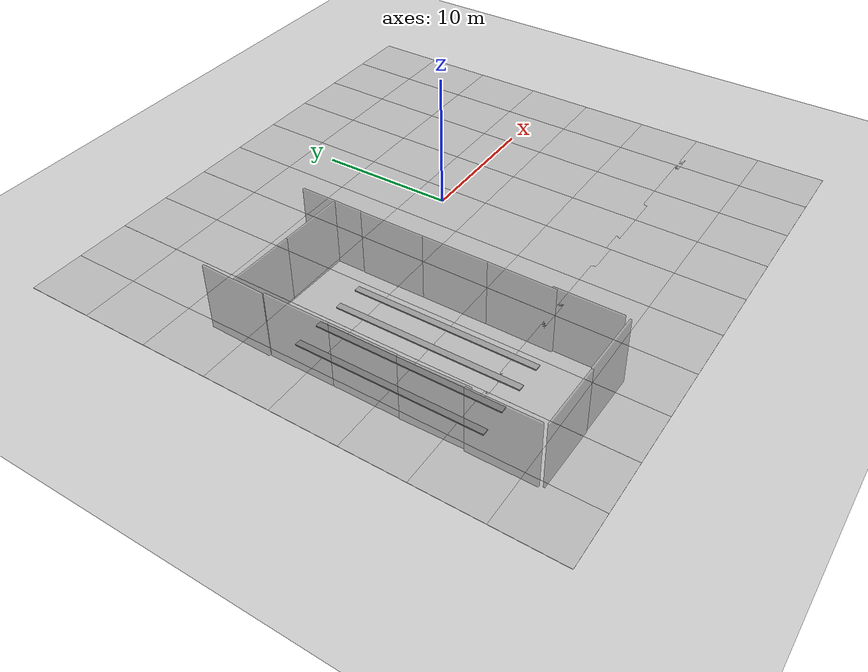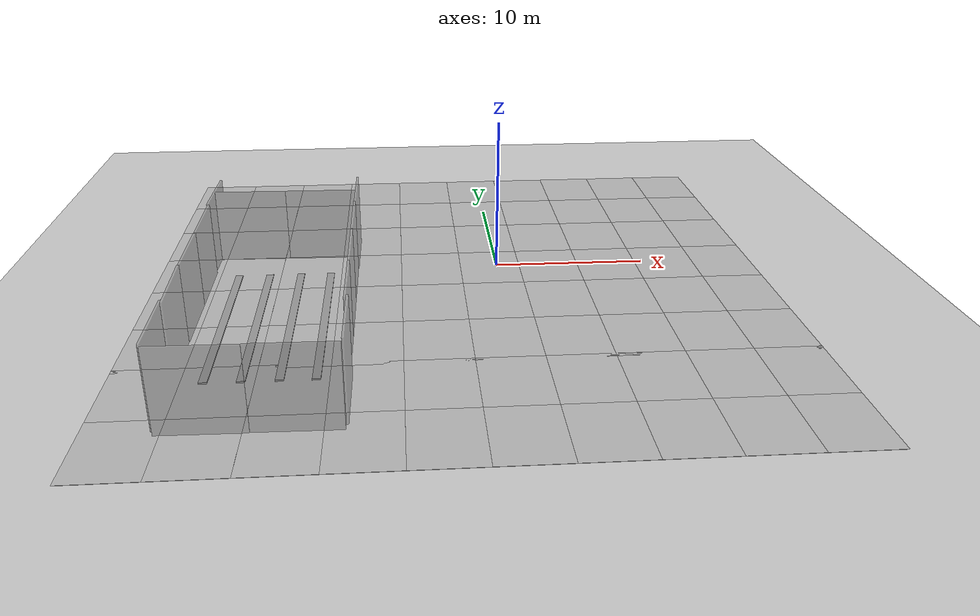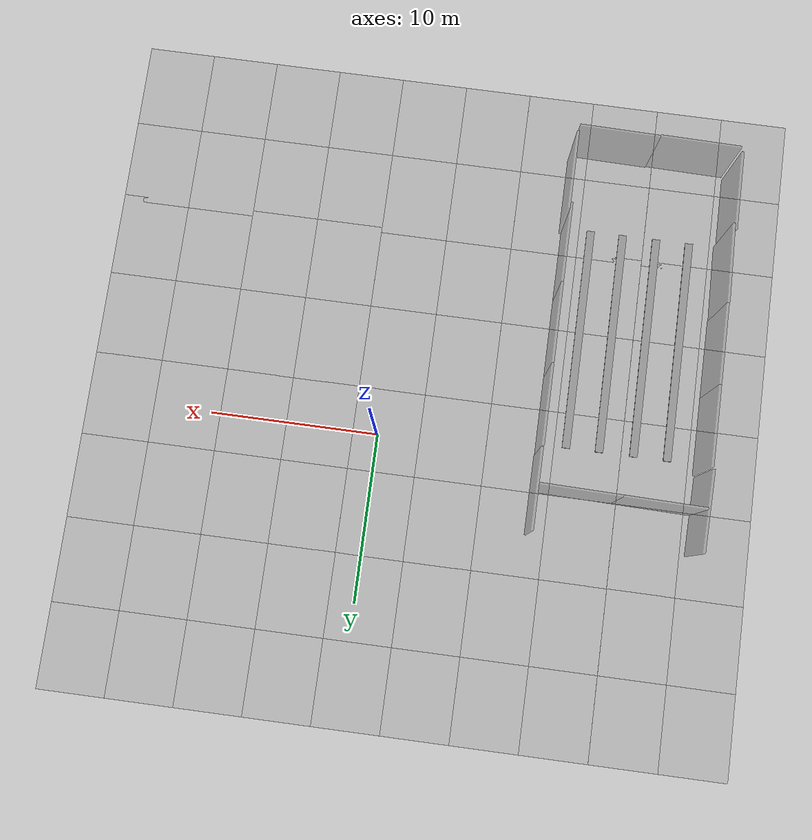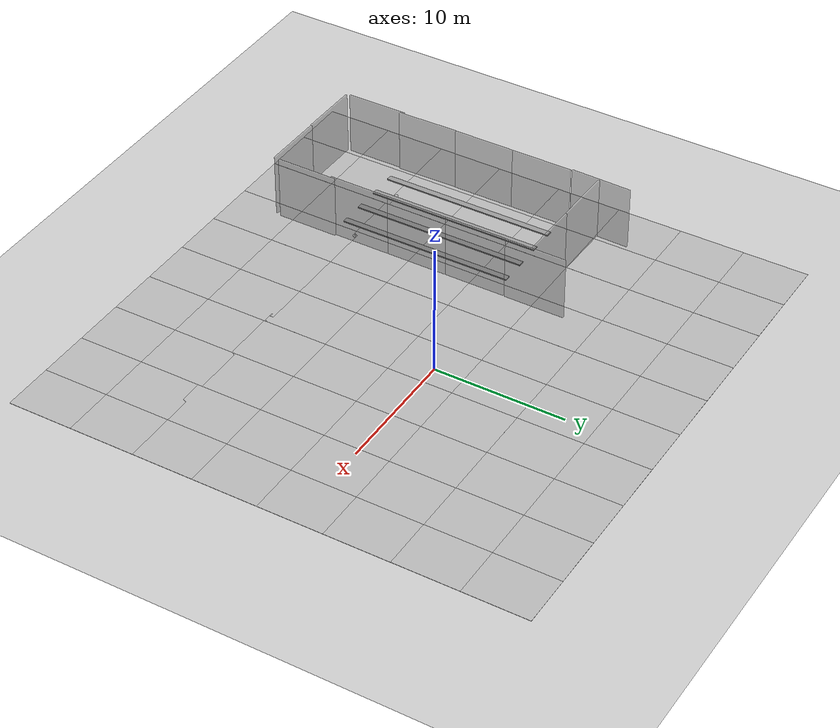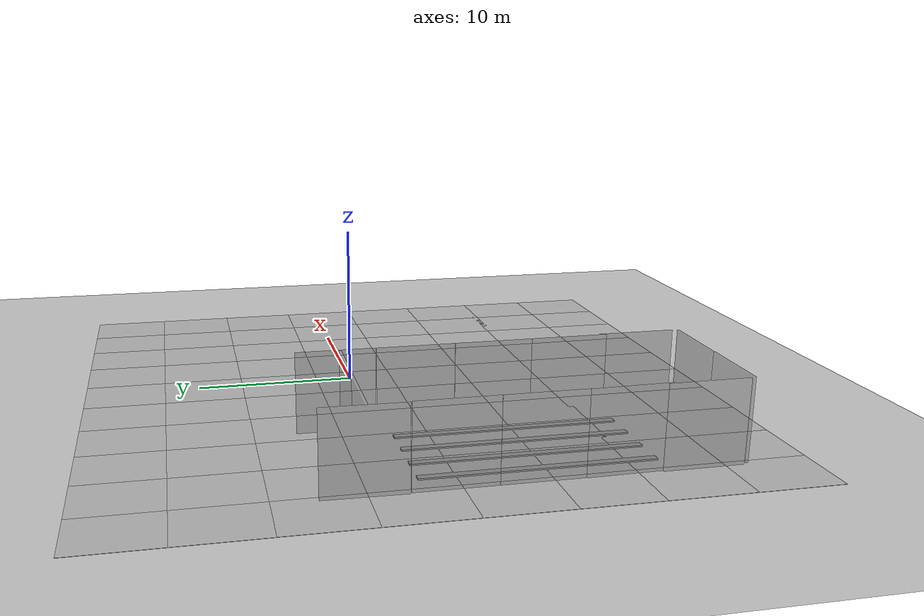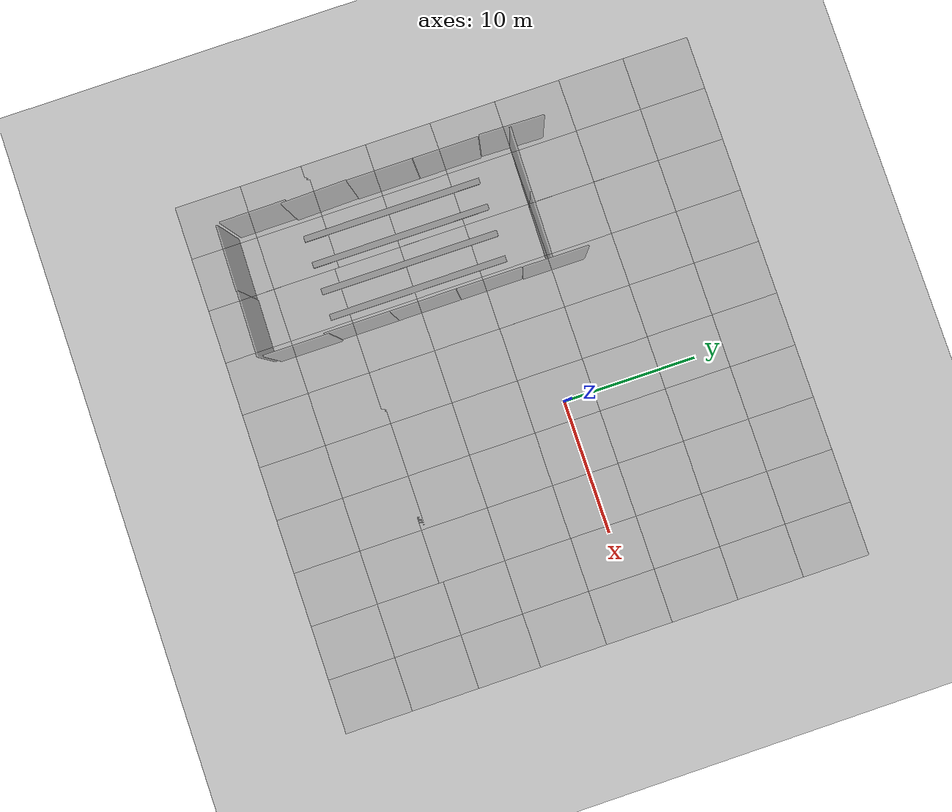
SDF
<sdf version="1.6">
 <world name="default">
  <light name="sun" type="directional">
   <pose>0 0 10 0 -0 0</pose>
   <diffuse>0.8 0.8 0.8 1</diffuse>
   <specular>0.2 0.2 0.2 1</specular>
   <attenuation>
    <range>1000</range>
    <constant>0.9</constant>
    <linear>0.01</linear>
    <quadratic>0.001</quadratic>
   </attenuation>
   <direction>-0.5 0.1 -0.9</direction>
  </light>
  <scene>
   <sky><clouds><speed>12</speed></clouds></sky>
   <ambient>0.4 0.4 0.4 1</ambient>
   <background>0.7 0.7 0.7 1</background>
   <shadows>1</shadows>
  </scene>
  <model name="ground_plane">
   <static>1</static>
   <link name="link">
    <collision name="collision">
     <geometry><plane><normal>0 0 1</normal><size>100 100</size></plane></geometry>
     <surface>
      <contact><collide_bitmask>65535</collide_bitmask></contact>
      <friction><ode><mu>100</mu><mu2>50</mu2></ode></friction>
     </surface>
    </collision>
    <visual name="visual">
     <cast_shadows>0</cast_shadows>
     <geometry><plane><normal>0 0 1</normal><size>100 100</size></plane></geometry>
     <material>
      <script><uri>file://media/materials/scripts/gazebo.material</uri><name>Gazebo/Grey</name></script>
     </material>
    </visual>
   </link>
  </model>
  <gravity>0 0 -9.8</gravity>
  <magnetic_field>6e-06 2.3e-05 -4.2e-05</magnetic_field>
  <atmosphere type="adiabatic"/>
  <physics name="default_physics" default="0" type="ode">
   <max_step_size>0.001</max_step_size>
   <real_time_factor>1</real_time_factor>
   <real_time_update_rate>1000</real_time_update_rate>
  </physics>
  <scene><ambient>0.4 0.4 0.4 1</ambient><background>0.7 0.7 0.7 1</background><shadows>1</shadows></scene>
  <audio><device>default</device></audio>
  <spherical_coordinates>
   <surface_model>EARTH_WGS84</surface_model>
   <latitude_deg>0</latitude_deg>
   <longitude_deg>0</longitude_deg>
   <elevation>0</elevation>
   <heading_deg>0</heading_deg>
  </spherical_coordinates>
  <model name="Box_24x15W_0">
   <link name="Wall">
    <pose>0 0 0.1985 0 -0 0</pose>
    <inertial>
     <mass>5</mass>
     <inertia><ixx>0.1022</ixx><iyy>0.2197</iyy><izz>0.1905</izz><ixy>0</ixy><ixz>0</ixz><iyz>0</iyz></inertia>
    </inertial>
    <collision name="Wall_Collision">
     <geometry><box><size>0.470639 13.5 0.091294</size></box></geometry>
    </collision>
    <visual name="Wall_Visual">
     <geometry><box><size>0.470639 13.5 0.091294</size></box></geometry>
     <material>
      <script><uri>file://media/materials/scripts/gazebo.material</uri><name>Gazebo/Grey</name></script>
      <ambient>1 1 1 1</ambient>
     </material>
    </visual>
   </link>
   <static>1</static>
   <pose>-15.2421 -7.42472 -0.146343 0 -0 0</pose>
  </model>
  <model name="Box_24x15W">
   <link name="Wall">
    <pose>0 0 0.1985 0 -0 0</pose>
    <inertial>
     <mass>5</mass>
     <inertia><ixx>0.1022</ixx><iyy>0.2197</iyy><izz>0.1905</izz><ixy>0</ixy><ixz>0</ixz><iyz>0</iyz></inertia>
    </inertial>
    <collision name="Wall_Collision">
     <geometry><box><size>0.470639 13.5 0.091294</size></box></geometry>
    </collision>
    <visual name="Wall_Visual">
     <geometry><box><size>0.470639 13.5 0.091294</size></box></geometry>
     <material>
      <script><uri>file://media/materials/scripts/gazebo.material</uri><name>Gazebo/Grey</name></script>
      <ambient>1 1 1 1</ambient>
     </material>
    </visual>
   </link>
   <static>1</static>
   <pose>-17.2564 -7.42472 -0.14031 0 -0 0</pose>
  </model>
  <model name="Box_24x15W_0_clone">
   <link name="Wall">
    <pose>0 0 0.1985 0 -0 0</pose>
    <inertial>
     <mass>5</mass>
     <inertia><ixx>0.1022</ixx><iyy>0.2197</iyy><izz>0.1905</izz><ixy>0</ixy><ixz>0</ixz><iyz>0</iyz></inertia>
    </inertial>
    <collision name="Wall_Collision">
     <geometry><box><size>0.470639 13.5 0.091294</size></box></geometry>
    </collision>
    <visual name="Wall_Visual">
     <geometry><box><size>0.470639 13.5 0.091294</size></box></geometry>
     <material>
      <script><uri>file://media/materials/scripts/gazebo.material</uri><name>Gazebo/Grey</name></script>
      <ambient>1 1 1 1</ambient>
     </material>
    </visual>
   </link>
   <static>1</static>
   <pose>-13.1875 -7.42472 -0.140264 0 -0 0</pose>
  </model>
  <model name="Box_24x15W_0_clone_clone">
   <link name="Wall">
    <pose>0 0 0.1985 0 -0 0</pose>
    <inertial>
     <mass>5</mass>
     <inertia><ixx>0.1022</ixx><iyy>0.2197</iyy><izz>0.1905</izz><ixy>0</ixy><ixz>0</ixz><iyz>0</iyz></inertia>
    </inertial>
    <collision name="Wall_Collision">
     <geometry><box><size>0.470639 13.5 0.091294</size></box></geometry>
    </collision>
    <visual name="Wall_Visual">
     <geometry><box><size>0.470639 13.5 0.091294</size></box></geometry>
     <material>
      <script><uri>file://media/materials/scripts/gazebo.material</uri><name>Gazebo/Grey</name></script>
      <ambient>1 1 1 1</ambient>
     </material>
    </visual>
   </link>
   <static>1</static>
   <pose>-11.214 -7.42472 -0.140264 0 -0 0</pose>
  </model>
  <model name="Ground_Soil">
   <model name="mud_box">
    <static>1</static>
    <link name="link">
     <collision name="collision"><geometry><box><size>8 10 0.02</size></box></geometry></collision>
     <visual name="visual_1">
      <pose>-2 2.5 0 0 -0 0</pose>
      <cast_shadows>0</cast_shadows>
      <geometry><box><size>4 5 0.02</size></box></geometry>
      <material>
       <script>
        <uri>model://mud_box/materials/scripts</uri>
        <uri>model://mud_box/materials/textures</uri>
        <name>vrc/mud</name>
       </script>
      </material>
     </visual>
     <visual name="visual_2">
      <pose>2 2.5 0 0 -0 0</pose>
      <cast_shadows>0</cast_shadows>
      <geometry><box><size>4 5 0.02</size></box></geometry>
      <material>
       <script>
        <uri>model://mud_box/materials/scripts</uri>
        <uri>model://mud_box/materials/textures</uri>
        <name>vrc/mud</name>
       </script>
      </material>
     </visual>
     <visual name="visual_3">
      <pose>2 -2.5 0 0 -0 0</pose>
      <cast_shadows>0</cast_shadows>
      <geometry><box><size>4 5 0.02</size></box></geometry>
      <material>
       <script>
        <uri>model://mud_box/materials/scripts</uri>
        <uri>model://mud_box/materials/textures</uri>
        <name>vrc/mud</name>
       </script>
      </material>
     </visual>
     <visual name="visual_4">
      <pose>-2 -2.5 0 0 -0 0</pose>
      <cast_shadows>0</cast_shadows>
      <geometry><box><size>4 5 0.02</size></box></geometry>
      <material>
       <script>
        <uri>model://mud_box/materials/scripts</uri>
        <uri>model://mud_box/materials/textures</uri>
        <name>vrc/mud</name>
       </script>
      </material>
     </visual>
    </link>
    <pose>-16.0013 0.000118 0 0 -0 0</pose>
   </model>
   <model name="mud_box_0">
    <static>1</static>
    <link name="link">
     <collision name="collision"><geometry><box><size>8 10 0.02</size></box></geometry></collision>
     <visual name="visual_1">
      <pose>-2 2.5 0 0 -0 0</pose>
      <cast_shadows>0</cast_shadows>
      <geometry><box><size>4 5 0.02</size></box></geometry>
      <material>
       <script>
        <uri>model://mud_box/materials/scripts</uri>
        <uri>model://mud_box/materials/textures</uri>
        <name>vrc/mud</name>
       </script>
      </material>
     </visual>
     <visual name="visual_2">
      <pose>2 2.5 0 0 -0 0</pose>
      <cast_shadows>0</cast_shadows>
      <geometry><box><size>4 5 0.02</size></box></geometry>
      <material>
       <script>
        <uri>model://mud_box/materials/scripts</uri>
        <uri>model://mud_box/materials/textures</uri>
        <name>vrc/mud</name>
       </script>
      </material>
     </visual>
     <visual name="visual_3">
      <pose>2 -2.5 0 0 -0 0</pose>
      <cast_shadows>0</cast_shadows>
      <geometry><box><size>4 5 0.02</size></box></geometry>
      <material>
       <script>
        <uri>model://mud_box/materials/scripts</uri>
        <uri>model://mud_box/materials/textures</uri>
        <name>vrc/mud</name>
       </script>
      </material>
     </visual>
     <visual name="visual_4">
      <pose>-2 -2.5 0 0 -0 0</pose>
      <cast_shadows>0</cast_shadows>
      <geometry><box><size>4 5 0.02</size></box></geometry>
      <material>
       <script>
        <uri>model://mud_box/materials/scripts</uri>
        <uri>model://mud_box/materials/textures</uri>
        <name>vrc/mud</name>
       </script>
      </material>
     </visual>
    </link>
    <pose>-7.99939 9.1e-05 0 0 -0 0</pose>
   </model>
   <model name="mud_box_1">
    <static>1</static>
    <link name="link">
     <collision name="collision"><geometry><box><size>8 10 0.02</size></box></geometry></collision>
     <visual name="visual_1">
      <pose>-2 2.5 0 0 -0 0</pose>
      <cast_shadows>0</cast_shadows>
      <geometry><box><size>4 5 0.02</size></box></geometry>
      <material>
       <script>
        <uri>model://mud_box/materials/scripts</uri>
        <uri>model://mud_box/materials/textures</uri>
        <name>vrc/mud</name>
       </script>
      </material>
     </visual>
     <visual name="visual_2">
      <pose>2 2.5 0 0 -0 0</pose>
      <cast_shadows>0</cast_shadows>
      <geometry><box><size>4 5 0.02</size></box></geometry>
      <material>
       <script>
        <uri>model://mud_box/materials/scripts</uri>
        <uri>model://mud_box/materials/textures</uri>
        <name>vrc/mud</name>
       </script>
      </material>
     </visual>
     <visual name="visual_3">
      <pose>2 -2.5 0 0 -0 0</pose>
      <cast_shadows>0</cast_shadows>
      <geometry><box><size>4 5 0.02</size></box></geometry>
      <material>
       <script>
        <uri>model://mud_box/materials/scripts</uri>
        <uri>model://mud_box/materials/textures</uri>
        <name>vrc/mud</name>
       </script>
      </material>
     </visual>
     <visual name="visual_4">
      <pose>-2 -2.5 0 0 -0 0</pose>
      <cast_shadows>0</cast_shadows>
      <geometry><box><size>4 5 0.02</size></box></geometry>
      <material>
       <script>
        <uri>model://mud_box/materials/scripts</uri>
        <uri>model://mud_box/materials/textures</uri>
        <name>vrc/mud</name>
       </script>
      </material>
     </visual>
    </link>
    <pose>0.000809 -0.000342 0 0 -0 0</pose>
   </model>
   <model name="mud_box_2">
    <static>1</static>
    <link name="link">
     <collision name="collision"><geometry><box><size>8 10 0.02</size></box></geometry></collision>
     <visual name="visual_1">
      <pose>-2 2.5 0 0 -0 0</pose>
      <cast_shadows>0</cast_shadows>
      <geometry><box><size>4 5 0.02</size></box></geometry>
      <material>
       <script>
        <uri>model://mud_box/materials/scripts</uri>
        <uri>model://mud_box/materials/textures</uri>
        <name>vrc/mud</name>
       </script>
      </material>
     </visual>
     <visual name="visual_2">
      <pose>2 2.5 0 0 -0 0</pose>
      <cast_shadows>0</cast_shadows>
      <geometry><box><size>4 5 0.02</size></box></geometry>
      <material>
       <script>
        <uri>model://mud_box/materials/scripts</uri>
        <uri>model://mud_box/materials/textures</uri>
        <name>vrc/mud</name>
       </script>
      </material>
     </visual>
     <visual name="visual_3">
      <pose>2 -2.5 0 0 -0 0</pose>
      <cast_shadows>0</cast_shadows>
      <geometry><box><size>4 5 0.02</size></box></geometry>
      <material>
       <script>
        <uri>model://mud_box/materials/scripts</uri>
        <uri>model://mud_box/materials/textures</uri>
        <name>vrc/mud</name>
       </script>
      </material>
     </visual>
     <visual name="visual_4">
      <pose>-2 -2.5 0 0 -0 0</pose>
      <cast_shadows>0</cast_shadows>
      <geometry><box><size>4 5 0.02</size></box></geometry>
      <material>
       <script>
        <uri>model://mud_box/materials/scripts</uri>
        <uri>model://mud_box/materials/textures</uri>
        <name>vrc/mud</name>
       </script>
      </material>
     </visual>
    </link>
    <pose>8.00089 -0.000148 0 0 -0 0</pose>
   </model>
   <model name="mud_box_3">
    <static>1</static>
    <link name="link">
     <collision name="collision"><geometry><box><size>8 10 0.02</size></box></geometry></collision>
     <visual name="visual_1">
      <pose>-2 2.5 0 0 -0 0</pose>
      <cast_shadows>0</cast_shadows>
      <geometry><box><size>4 5 0.02</size></box></geometry>
      <material>
       <script>
        <uri>model://mud_box/materials/scripts</uri>
        <uri>model://mud_box/materials/textures</uri>
        <name>vrc/mud</name>
       </script>
      </material>
     </visual>
     <visual name="visual_2">
      <pose>2 2.5 0 0 -0 0</pose>
      <cast_shadows>0</cast_shadows>
      <geometry><box><size>4 5 0.02</size></box></geometry>
      <material>
       <script>
        <uri>model://mud_box/materials/scripts</uri>
        <uri>model://mud_box/materials/textures</uri>
        <name>vrc/mud</name>
       </script>
      </material>
     </visual>
     <visual name="visual_3">
      <pose>2 -2.5 0 0 -0 0</pose>
      <cast_shadows>0</cast_shadows>
      <geometry><box><size>4 5 0.02</size></box></geometry>
      <material>
       <script>
        <uri>model://mud_box/materials/scripts</uri>
        <uri>model://mud_box/materials/textures</uri>
        <name>vrc/mud</name>
       </script>
      </material>
     </visual>
     <visual name="visual_4">
      <pose>-2 -2.5 0 0 -0 0</pose>
      <cast_shadows>0</cast_shadows>
      <geometry><box><size>4 5 0.02</size></box></geometry>
      <material>
       <script>
        <uri>model://mud_box/materials/scripts</uri>
        <uri>model://mud_box/materials/textures</uri>
        <name>vrc/mud</name>
       </script>
      </material>
     </visual>
    </link>
    <pose>15.9991 0.000313 0 0 -0 0</pose>
   </model>
   <static>0</static>
   <pose>-2.5023 -17.4296 0 0 -0 0</pose>
  </model>
  <model name="Ground_Soil_0">
   <model name="mud_box">
    <static>1</static>
    <link name="link">
     <collision name="collision"><geometry><box><size>8 10 0.02</size></box></geometry></collision>
     <visual name="visual_1">
      <pose>-2 2.5 0 0 -0 0</pose>
      <cast_shadows>0</cast_shadows>
      <geometry><box><size>4 5 0.02</size></box></geometry>
      <material>
       <script>
        <uri>model://mud_box/materials/scripts</uri>
        <uri>model://mud_box/materials/textures</uri>
        <name>vrc/mud</name>
       </script>
      </material>
     </visual>
     <visual name="visual_2">
      <pose>2 2.5 0 0 -0 0</pose>
      <cast_shadows>0</cast_shadows>
      <geometry><box><size>4 5 0.02</size></box></geometry>
      <material>
       <script>
        <uri>model://mud_box/materials/scripts</uri>
        <uri>model://mud_box/materials/textures</uri>
        <name>vrc/mud</name>
       </script>
      </material>
     </visual>
     <visual name="visual_3">
      <pose>2 -2.5 0 0 -0 0</pose>
      <cast_shadows>0</cast_shadows>
      <geometry><box><size>4 5 0.02</size></box></geometry>
      <material>
       <script>
        <uri>model://mud_box/materials/scripts</uri>
        <uri>model://mud_box/materials/textures</uri>
        <name>vrc/mud</name>
       </script>
      </material>
     </visual>
     <visual name="visual_4">
      <pose>-2 -2.5 0 0 -0 0</pose>
      <cast_shadows>0</cast_shadows>
      <geometry><box><size>4 5 0.02</size></box></geometry>
      <material>
       <script>
        <uri>model://mud_box/materials/scripts</uri>
        <uri>model://mud_box/materials/textures</uri>
        <name>vrc/mud</name>
       </script>
      </material>
     </visual>
    </link>
    <pose>-16.0013 0.000118 0 0 -0 0</pose>
   </model>
   <model name="mud_box_0">
    <static>1</static>
    <link name="link">
     <collision name="collision"><geometry><box><size>8 10 0.02</size></box></geometry></collision>
     <visual name="visual_1">
      <pose>-2 2.5 0 0 -0 0</pose>
      <cast_shadows>0</cast_shadows>
      <geometry><box><size>4 5 0.02</size></box></geometry>
      <material>
       <script>
        <uri>model://mud_box/materials/scripts</uri>
        <uri>model://mud_box/materials/textures</uri>
        <name>vrc/mud</name>
       </script>
      </material>
     </visual>
     <visual name="visual_2">
      <pose>2 2.5 0 0 -0 0</pose>
      <cast_shadows>0</cast_shadows>
      <geometry><box><size>4 5 0.02</size></box></geometry>
      <material>
       <script>
        <uri>model://mud_box/materials/scripts</uri>
        <uri>model://mud_box/materials/textures</uri>
        <name>vrc/mud</name>
       </script>
      </material>
     </visual>
     <visual name="visual_3">
      <pose>2 -2.5 0 0 -0 0</pose>
      <cast_shadows>0</cast_shadows>
      <geometry><box><size>4 5 0.02</size></box></geometry>
      <material>
       <script>
        <uri>model://mud_box/materials/scripts</uri>
        <uri>model://mud_box/materials/textures</uri>
        <name>vrc/mud</name>
       </script>
      </material>
     </visual>
     <visual name="visual_4">
      <pose>-2 -2.5 0 0 -0 0</pose>
      <cast_shadows>0</cast_shadows>
      <geometry><box><size>4 5 0.02</size></box></geometry>
      <material>
       <script>
        <uri>model://mud_box/materials/scripts</uri>
        <uri>model://mud_box/materials/textures</uri>
        <name>vrc/mud</name>
       </script>
      </material>
     </visual>
    </link>
    <pose>-7.99939 9.1e-05 0 0 -0 0</pose>
   </model>
   <model name="mud_box_1">
    <static>1</static>
    <link name="link">
     <collision name="collision"><geometry><box><size>8 10 0.02</size></box></geometry></collision>
     <visual name="visual_1">
      <pose>-2 2.5 0 0 -0 0</pose>
      <cast_shadows>0</cast_shadows>
      <geometry><box><size>4 5 0.02</size></box></geometry>
      <material>
       <script>
        <uri>model://mud_box/materials/scripts</uri>
        <uri>model://mud_box/materials/textures</uri>
        <name>vrc/mud</name>
       </script>
      </material>
     </visual>
     <visual name="visual_2">
      <pose>2 2.5 0 0 -0 0</pose>
      <cast_shadows>0</cast_shadows>
      <geometry><box><size>4 5 0.02</size></box></geometry>
      <material>
       <script>
        <uri>model://mud_box/materials/scripts</uri>
        <uri>model://mud_box/materials/textures</uri>
        <name>vrc/mud</name>
       </script>
      </material>
     </visual>
     <visual name="visual_3">
      <pose>2 -2.5 0 0 -0 0</pose>
      <cast_shadows>0</cast_shadows>
      <geometry><box><size>4 5 0.02</size></box></geometry>
      <material>
       <script>
        <uri>model://mud_box/materials/scripts</uri>
        <uri>model://mud_box/materials/textures</uri>
        <name>vrc/mud</name>
       </script>
      </material>
     </visual>
     <visual name="visual_4">
      <pose>-2 -2.5 0 0 -0 0</pose>
      <cast_shadows>0</cast_shadows>
      <geometry><box><size>4 5 0.02</size></box></geometry>
      <material>
       <script>
        <uri>model://mud_box/materials/scripts</uri>
        <uri>model://mud_box/materials/textures</uri>
        <name>vrc/mud</name>
       </script>
      </material>
     </visual>
    </link>
    <pose>0.000809 -0.000342 0 0 -0 0</pose>
   </model>
   <model name="mud_box_2">
    <static>1</static>
    <link name="link">
     <collision name="collision"><geometry><box><size>8 10 0.02</size></box></geometry></collision>
     <visual name="visual_1">
      <pose>-2 2.5 0 0 -0 0</pose>
      <cast_shadows>0</cast_shadows>
      <geometry><box><size>4 5 0.02</size></box></geometry>
      <material>
       <script>
        <uri>model://mud_box/materials/scripts</uri>
        <uri>model://mud_box/materials/textures</uri>
        <name>vrc/mud</name>
       </script>
      </material>
     </visual>
     <visual name="visual_2">
      <pose>2 2.5 0 0 -0 0</pose>
      <cast_shadows>0</cast_shadows>
      <geometry><box><size>4 5 0.02</size></box></geometry>
      <material>
       <script>
        <uri>model://mud_box/materials/scripts</uri>
        <uri>model://mud_box/materials/textures</uri>
        <name>vrc/mud</name>
       </script>
      </material>
     </visual>
     <visual name="visual_3">
      <pose>2 -2.5 0 0 -0 0</pose>
      <cast_shadows>0</cast_shadows>
      <geometry><box><size>4 5 0.02</size></box></geometry>
      <material>
       <script>
        <uri>model://mud_box/materials/scripts</uri>
        <uri>model://mud_box/materials/textures</uri>
        <name>vrc/mud</name>
       </script>
      </material>
     </visual>
     <visual name="visual_4">
      <pose>-2 -2.5 0 0 -0 0</pose>
      <cast_shadows>0</cast_shadows>
      <geometry><box><size>4 5 0.02</size></box></geometry>
      <material>
       <script>
        <uri>model://mud_box/materials/scripts</uri>
        <uri>model://mud_box/materials/textures</uri>
        <name>vrc/mud</name>
       </script>
      </material>
     </visual>
    </link>
    <pose>8.00089 -0.000148 0 0 -0 0</pose>
   </model>
   <model name="mud_box_3">
    <static>1</static>
    <link name="link">
     <collision name="collision"><geometry><box><size>8 10 0.02</size></box></geometry></collision>
     <visual name="visual_1">
      <pose>-2 2.5 0 0 -0 0</pose>
      <cast_shadows>0</cast_shadows>
      <geometry><box><size>4 5 0.02</size></box></geometry>
      <material>
       <script>
        <uri>model://mud_box/materials/scripts</uri>
        <uri>model://mud_box/materials/textures</uri>
        <name>vrc/mud</name>
       </script>
      </material>
     </visual>
     <visual name="visual_2">
      <pose>2 2.5 0 0 -0 0</pose>
      <cast_shadows>0</cast_shadows>
      <geometry><box><size>4 5 0.02</size></box></geometry>
      <material>
       <script>
        <uri>model://mud_box/materials/scripts</uri>
        <uri>model://mud_box/materials/textures</uri>
        <name>vrc/mud</name>
       </script>
      </material>
     </visual>
     <visual name="visual_3">
      <pose>2 -2.5 0 0 -0 0</pose>
      <cast_shadows>0</cast_shadows>
      <geometry><box><size>4 5 0.02</size></box></geometry>
      <material>
       <script>
        <uri>model://mud_box/materials/scripts</uri>
        <uri>model://mud_box/materials/textures</uri>
        <name>vrc/mud</name>
       </script>
      </material>
     </visual>
     <visual name="visual_4">
      <pose>-2 -2.5 0 0 -0 0</pose>
      <cast_shadows>0</cast_shadows>
      <geometry><box><size>4 5 0.02</size></box></geometry>
      <material>
       <script>
        <uri>model://mud_box/materials/scripts</uri>
        <uri>model://mud_box/materials/textures</uri>
        <name>vrc/mud</name>
       </script>
      </material>
     </visual>
    </link>
    <pose>15.9991 0.000313 0 0 -0 0</pose>
   </model>
   <static>0</static>
   <pose>-2.5023 -7.75753 0 0 -0 0</pose>
  </model>
  <model name="Ground_Soil_1">
   <model name="mud_box">
    <static>1</static>
    <link name="link">
     <collision name="collision"><geometry><box><size>8 10 0.02</size></box></geometry></collision>
     <visual name="visual_1">
      <pose>-2 2.5 0 0 -0 0</pose>
      <cast_shadows>0</cast_shadows>
      <geometry><box><size>4 5 0.02</size></box></geometry>
      <material>
       <script>
        <uri>model://mud_box/materials/scripts</uri>
        <uri>model://mud_box/materials/textures</uri>
        <name>vrc/mud</name>
       </script>
      </material>
     </visual>
     <visual name="visual_2">
      <pose>2 2.5 0 0 -0 0</pose>
      <cast_shadows>0</cast_shadows>
      <geometry><box><size>4 5 0.02</size></box></geometry>
      <material>
       <script>
        <uri>model://mud_box/materials/scripts</uri>
        <uri>model://mud_box/materials/textures</uri>
        <name>vrc/mud</name>
       </script>
      </material>
     </visual>
     <visual name="visual_3">
      <pose>2 -2.5 0 0 -0 0</pose>
      <cast_shadows>0</cast_shadows>
      <geometry><box><size>4 5 0.02</size></box></geometry>
      <material>
       <script>
        <uri>model://mud_box/materials/scripts</uri>
        <uri>model://mud_box/materials/textures</uri>
        <name>vrc/mud</name>
       </script>
      </material>
     </visual>
     <visual name="visual_4">
      <pose>-2 -2.5 0 0 -0 0</pose>
      <cast_shadows>0</cast_shadows>
      <geometry><box><size>4 5 0.02</size></box></geometry>
      <material>
       <script>
        <uri>model://mud_box/materials/scripts</uri>
        <uri>model://mud_box/materials/textures</uri>
        <name>vrc/mud</name>
       </script>
      </material>
     </visual>
    </link>
    <pose>-16.0013 0.000118 0 0 -0 0</pose>
   </model>
   <model name="mud_box_0">
    <static>1</static>
    <link name="link">
     <collision name="collision"><geometry><box><size>8 10 0.02</size></box></geometry></collision>
     <visual name="visual_1">
      <pose>-2 2.5 0 0 -0 0</pose>
      <cast_shadows>0</cast_shadows>
      <geometry><box><size>4 5 0.02</size></box></geometry>
      <material>
       <script>
        <uri>model://mud_box/materials/scripts</uri>
        <uri>model://mud_box/materials/textures</uri>
        <name>vrc/mud</name>
       </script>
      </material>
     </visual>
     <visual name="visual_2">
      <pose>2 2.5 0 0 -0 0</pose>
      <cast_shadows>0</cast_shadows>
      <geometry><box><size>4 5 0.02</size></box></geometry>
      <material>
       <script>
        <uri>model://mud_box/materials/scripts</uri>
        <uri>model://mud_box/materials/textures</uri>
        <name>vrc/mud</name>
       </script>
      </material>
     </visual>
     <visual name="visual_3">
      <pose>2 -2.5 0 0 -0 0</pose>
      <cast_shadows>0</cast_shadows>
      <geometry><box><size>4 5 0.02</size></box></geometry>
      <material>
       <script>
        <uri>model://mud_box/materials/scripts</uri>
        <uri>model://mud_box/materials/textures</uri>
        <name>vrc/mud</name>
       </script>
      </material>
     </visual>
     <visual name="visual_4">
      <pose>-2 -2.5 0 0 -0 0</pose>
      <cast_shadows>0</cast_shadows>
      <geometry><box><size>4 5 0.02</size></box></geometry>
      <material>
       <script>
        <uri>model://mud_box/materials/scripts</uri>
        <uri>model://mud_box/materials/textures</uri>
        <name>vrc/mud</name>
       </script>
      </material>
     </visual>
    </link>
    <pose>-7.99939 9.1e-05 0 0 -0 0</pose>
   </model>
   <model name="mud_box_1">
    <static>1</static>
    <link name="link">
     <collision name="collision"><geometry><box><size>8 10 0.02</size></box></geometry></collision>
     <visual name="visual_1">
      <pose>-2 2.5 0 0 -0 0</pose>
      <cast_shadows>0</cast_shadows>
      <geometry><box><size>4 5 0.02</size></box></geometry>
      <material>
       <script>
        <uri>model://mud_box/materials/scripts</uri>
        <uri>model://mud_box/materials/textures</uri>
        <name>vrc/mud</name>
       </script>
      </material>
     </visual>
     <visual name="visual_2">
      <pose>2 2.5 0 0 -0 0</pose>
      <cast_shadows>0</cast_shadows>
      <geometry><box><size>4 5 0.02</size></box></geometry>
      <material>
       <script>
        <uri>model://mud_box/materials/scripts</uri>
        <uri>model://mud_box/materials/textures</uri>
        <name>vrc/mud</name>
       </script>
      </material>
     </visual>
     <visual name="visual_3">
      <pose>2 -2.5 0 0 -0 0</pose>
      <cast_shadows>0</cast_shadows>
      <geometry><box><size>4 5 0.02</size></box></geometry>
      <material>
       <script>
        <uri>model://mud_box/materials/scripts</uri>
        <uri>model://mud_box/materials/textures</uri>
        <name>vrc/mud</name>
       </script>
      </material>
     </visual>
     <visual name="visual_4">
      <pose>-2 -2.5 0 0 -0 0</pose>
      <cast_shadows>0</cast_shadows>
      <geometry><box><size>4 5 0.02</size></box></geometry>
      <material>
       <script>
        <uri>model://mud_box/materials/scripts</uri>
        <uri>model://mud_box/materials/textures</uri>
        <name>vrc/mud</name>
       </script>
      </material>
     </visual>
    </link>
    <pose>0.000809 -0.000342 0 0 -0 0</pose>
   </model>
   <model name="mud_box_2">
    <static>1</static>
    <link name="link">
     <collision name="collision"><geometry><box><size>8 10 0.02</size></box></geometry></collision>
     <visual name="visual_1">
      <pose>-2 2.5 0 0 -0 0</pose>
      <cast_shadows>0</cast_shadows>
      <geometry><box><size>4 5 0.02</size></box></geometry>
      <material>
       <script>
        <uri>model://mud_box/materials/scripts</uri>
        <uri>model://mud_box/materials/textures</uri>
        <name>vrc/mud</name>
       </script>
      </material>
     </visual>
     <visual name="visual_2">
      <pose>2 2.5 0 0 -0 0</pose>
      <cast_shadows>0</cast_shadows>
      <geometry><box><size>4 5 0.02</size></box></geometry>
      <material>
       <script>
        <uri>model://mud_box/materials/scripts</uri>
        <uri>model://mud_box/materials/textures</uri>
        <name>vrc/mud</name>
       </script>
      </material>
     </visual>
     <visual name="visual_3">
      <pose>2 -2.5 0 0 -0 0</pose>
      <cast_shadows>0</cast_shadows>
      <geometry><box><size>4 5 0.02</size></box></geometry>
      <material>
       <script>
        <uri>model://mud_box/materials/scripts</uri>
        <uri>model://mud_box/materials/textures</uri>
        <name>vrc/mud</name>
       </script>
      </material>
     </visual>
     <visual name="visual_4">
      <pose>-2 -2.5 0 0 -0 0</pose>
      <cast_shadows>0</cast_shadows>
      <geometry><box><size>4 5 0.02</size></box></geometry>
      <material>
       <script>
        <uri>model://mud_box/materials/scripts</uri>
        <uri>model://mud_box/materials/textures</uri>
        <name>vrc/mud</name>
       </script>
      </material>
     </visual>
    </link>
    <pose>8.00089 -0.000148 0 0 -0 0</pose>
   </model>
   <model name="mud_box_3">
    <static>1</static>
    <link name="link">
     <collision name="collision"><geometry><box><size>8 10 0.02</size></box></geometry></collision>
     <visual name="visual_1">
      <pose>-2 2.5 0 0 -0 0</pose>
      <cast_shadows>0</cast_shadows>
      <geometry><box><size>4 5 0.02</size></box></geometry>
      <material>
       <script>
        <uri>model://mud_box/materials/scripts</uri>
        <uri>model://mud_box/materials/textures</uri>
        <name>vrc/mud</name>
       </script>
      </material>
     </visual>
     <visual name="visual_2">
      <pose>2 2.5 0 0 -0 0</pose>
      <cast_shadows>0</cast_shadows>
      <geometry><box><size>4 5 0.02</size></box></geometry>
      <material>
       <script>
        <uri>model://mud_box/materials/scripts</uri>
        <uri>model://mud_box/materials/textures</uri>
        <name>vrc/mud</name>
       </script>
      </material>
     </visual>
     <visual name="visual_3">
      <pose>2 -2.5 0 0 -0 0</pose>
      <cast_shadows>0</cast_shadows>
      <geometry><box><size>4 5 0.02</size></box></geometry>
      <material>
       <script>
        <uri>model://mud_box/materials/scripts</uri>
        <uri>model://mud_box/materials/textures</uri>
        <name>vrc/mud</name>
       </script>
      </material>
     </visual>
     <visual name="visual_4">
      <pose>-2 -2.5 0 0 -0 0</pose>
      <cast_shadows>0</cast_shadows>
      <geometry><box><size>4 5 0.02</size></box></geometry>
      <material>
       <script>
        <uri>model://mud_box/materials/scripts</uri>
        <uri>model://mud_box/materials/textures</uri>
        <name>vrc/mud</name>
       </script>
      </material>
     </visual>
    </link>
    <pose>15.9991 0.000313 0 0 -0 0</pose>
   </model>
   <static>0</static>
   <pose>-2.5027 2.22713 0 0 -0 0</pose>
  </model>
  <model name="Ground_Soil_2">
   <model name="mud_box">
    <static>1</static>
    <link name="link">
     <collision name="collision"><geometry><box><size>8 10 0.02</size></box></geometry></collision>
     <visual name="visual_1">
      <pose>-2 2.5 0 0 -0 0</pose>
      <cast_shadows>0</cast_shadows>
      <geometry><box><size>4 5 0.02</size></box></geometry>
      <material>
       <script>
        <uri>model://mud_box/materials/scripts</uri>
        <uri>model://mud_box/materials/textures</uri>
        <name>vrc/mud</name>
       </script>
      </material>
     </visual>
     <visual name="visual_2">
      <pose>2 2.5 0 0 -0 0</pose>
      <cast_shadows>0</cast_shadows>
      <geometry><box><size>4 5 0.02</size></box></geometry>
      <material>
       <script>
        <uri>model://mud_box/materials/scripts</uri>
        <uri>model://mud_box/materials/textures</uri>
        <name>vrc/mud</name>
       </script>
      </material>
     </visual>
     <visual name="visual_3">
      <pose>2 -2.5 0 0 -0 0</pose>
      <cast_shadows>0</cast_shadows>
      <geometry><box><size>4 5 0.02</size></box></geometry>
      <material>
       <script>
        <uri>model://mud_box/materials/scripts</uri>
        <uri>model://mud_box/materials/textures</uri>
        <name>vrc/mud</name>
       </script>
      </material>
     </visual>
     <visual name="visual_4">
      <pose>-2 -2.5 0 0 -0 0</pose>
      <cast_shadows>0</cast_shadows>
      <geometry><box><size>4 5 0.02</size></box></geometry>
      <material>
       <script>
        <uri>model://mud_box/materials/scripts</uri>
        <uri>model://mud_box/materials/textures</uri>
        <name>vrc/mud</name>
       </script>
      </material>
     </visual>
    </link>
    <pose>-16.0013 0.000118 0 0 -0 0</pose>
   </model>
   <model name="mud_box_0">
    <static>1</static>
    <link name="link">
     <collision name="collision"><geometry><box><size>8 10 0.02</size></box></geometry></collision>
     <visual name="visual_1">
      <pose>-2 2.5 0 0 -0 0</pose>
      <cast_shadows>0</cast_shadows>
      <geometry><box><size>4 5 0.02</size></box></geometry>
      <material>
       <script>
        <uri>model://mud_box/materials/scripts</uri>
        <uri>model://mud_box/materials/textures</uri>
        <name>vrc/mud</name>
       </script>
      </material>
     </visual>
     <visual name="visual_2">
      <pose>2 2.5 0 0 -0 0</pose>
      <cast_shadows>0</cast_shadows>
      <geometry><box><size>4 5 0.02</size></box></geometry>
      <material>
       <script>
        <uri>model://mud_box/materials/scripts</uri>
        <uri>model://mud_box/materials/textures</uri>
        <name>vrc/mud</name>
       </script>
      </material>
     </visual>
     <visual name="visual_3">
      <pose>2 -2.5 0 0 -0 0</pose>
      <cast_shadows>0</cast_shadows>
      <geometry><box><size>4 5 0.02</size></box></geometry>
      <material>
       <script>
        <uri>model://mud_box/materials/scripts</uri>
        <uri>model://mud_box/materials/textures</uri>
        <name>vrc/mud</name>
       </script>
      </material>
     </visual>
     <visual name="visual_4">
      <pose>-2 -2.5 0 0 -0 0</pose>
      <cast_shadows>0</cast_shadows>
      <geometry><box><size>4 5 0.02</size></box></geometry>
      <material>
       <script>
        <uri>model://mud_box/materials/scripts</uri>
        <uri>model://mud_box/materials/textures</uri>
        <name>vrc/mud</name>
       </script>
      </material>
     </visual>
    </link>
    <pose>-7.99939 9.1e-05 0 0 -0 0</pose>
   </model>
   <model name="mud_box_1">
    <static>1</static>
    <link name="link">
     <collision name="collision"><geometry><box><size>8 10 0.02</size></box></geometry></collision>
     <visual name="visual_1">
      <pose>-2 2.5 0 0 -0 0</pose>
      <cast_shadows>0</cast_shadows>
      <geometry><box><size>4 5 0.02</size></box></geometry>
      <material>
       <script>
        <uri>model://mud_box/materials/scripts</uri>
        <uri>model://mud_box/materials/textures</uri>
        <name>vrc/mud</name>
       </script>
      </material>
     </visual>
     <visual name="visual_2">
      <pose>2 2.5 0 0 -0 0</pose>
      <cast_shadows>0</cast_shadows>
      <geometry><box><size>4 5 0.02</size></box></geometry>
      <material>
       <script>
        <uri>model://mud_box/materials/scripts</uri>
        <uri>model://mud_box/materials/textures</uri>
        <name>vrc/mud</name>
       </script>
      </material>
     </visual>
     <visual name="visual_3">
      <pose>2 -2.5 0 0 -0 0</pose>
      <cast_shadows>0</cast_shadows>
      <geometry><box><size>4 5 0.02</size></box></geometry>
      <material>
       <script>
        <uri>model://mud_box/materials/scripts</uri>
        <uri>model://mud_box/materials/textures</uri>
        <name>vrc/mud</name>
       </script>
      </material>
     </visual>
     <visual name="visual_4">
      <pose>-2 -2.5 0 0 -0 0</pose>
      <cast_shadows>0</cast_shadows>
      <geometry><box><size>4 5 0.02</size></box></geometry>
      <material>
       <script>
        <uri>model://mud_box/materials/scripts</uri>
        <uri>model://mud_box/materials/textures</uri>
        <name>vrc/mud</name>
       </script>
      </material>
     </visual>
    </link>
    <pose>0.000809 -0.000342 0 0 -0 0</pose>
   </model>
   <model name="mud_box_2">
    <static>1</static>
    <link name="link">
     <collision name="collision"><geometry><box><size>8 10 0.02</size></box></geometry></collision>
     <visual name="visual_1">
      <pose>-2 2.5 0 0 -0 0</pose>
      <cast_shadows>0</cast_shadows>
      <geometry><box><size>4 5 0.02</size></box></geometry>
      <material>
       <script>
        <uri>model://mud_box/materials/scripts</uri>
        <uri>model://mud_box/materials/textures</uri>
        <name>vrc/mud</name>
       </script>
      </material>
     </visual>
     <visual name="visual_2">
      <pose>2 2.5 0 0 -0 0</pose>
      <cast_shadows>0</cast_shadows>
      <geometry><box><size>4 5 0.02</size></box></geometry>
      <material>
       <script>
        <uri>model://mud_box/materials/scripts</uri>
        <uri>model://mud_box/materials/textures</uri>
        <name>vrc/mud</name>
       </script>
      </material>
     </visual>
     <visual name="visual_3">
      <pose>2 -2.5 0 0 -0 0</pose>
      <cast_shadows>0</cast_shadows>
      <geometry><box><size>4 5 0.02</size></box></geometry>
      <material>
       <script>
        <uri>model://mud_box/materials/scripts</uri>
        <uri>model://mud_box/materials/textures</uri>
        <name>vrc/mud</name>
       </script>
      </material>
     </visual>
     <visual name="visual_4">
      <pose>-2 -2.5 0 0 -0 0</pose>
      <cast_shadows>0</cast_shadows>
      <geometry><box><size>4 5 0.02</size></box></geometry>
      <material>
       <script>
        <uri>model://mud_box/materials/scripts</uri>
        <uri>model://mud_box/materials/textures</uri>
        <name>vrc/mud</name>
       </script>
      </material>
     </visual>
    </link>
    <pose>8.00089 -0.000148 0 0 -0 0</pose>
   </model>
   <model name="mud_box_3">
    <static>1</static>
    <link name="link">
     <collision name="collision"><geometry><box><size>8 10 0.02</size></box></geometry></collision>
     <visual name="visual_1">
      <pose>-2 2.5 0 0 -0 0</pose>
      <cast_shadows>0</cast_shadows>
      <geometry><box><size>4 5 0.02</size></box></geometry>
      <material>
       <script>
        <uri>model://mud_box/materials/scripts</uri>
        <uri>model://mud_box/materials/textures</uri>
        <name>vrc/mud</name>
       </script>
      </material>
     </visual>
     <visual name="visual_2">
      <pose>2 2.5 0 0 -0 0</pose>
      <cast_shadows>0</cast_shadows>
      <geometry><box><size>4 5 0.02</size></box></geometry>
      <material>
       <script>
        <uri>model://mud_box/materials/scripts</uri>
        <uri>model://mud_box/materials/textures</uri>
        <name>vrc/mud</name>
       </script>
      </material>
     </visual>
     <visual name="visual_3">
      <pose>2 -2.5 0 0 -0 0</pose>
      <cast_shadows>0</cast_shadows>
      <geometry><box><size>4 5 0.02</size></box></geometry>
      <material>
       <script>
        <uri>model://mud_box/materials/scripts</uri>
        <uri>model://mud_box/materials/textures</uri>
        <name>vrc/mud</name>
       </script>
      </material>
     </visual>
     <visual name="visual_4">
      <pose>-2 -2.5 0 0 -0 0</pose>
      <cast_shadows>0</cast_shadows>
      <geometry><box><size>4 5 0.02</size></box></geometry>
      <material>
       <script>
        <uri>model://mud_box/materials/scripts</uri>
        <uri>model://mud_box/materials/textures</uri>
        <name>vrc/mud</name>
       </script>
      </material>
     </visual>
    </link>
    <pose>15.9991 0.000313 0 0 -0 0</pose>
   </model>
   <static>0</static>
   <pose>-2.5134 12.2138 0 0 -0 0</pose>
  </model>
  <model name="wall_0">
   <link name="link">
    <inertial>
     <mass>2.87883</mass>
     <inertia><ixx>11.0771</ixx><ixy>0</ixy><ixz>0</ixz><iyy>5.80298</iyy><iyz>0</iyz><izz>5.28163</izz></inertia>
    </inertial>
    <pose>0 -0.040293 1.94803 0 -0 0</pose>
    <visual name="visual">
     <geometry><box><size>0.12484 4.69043 4.91663</size></box></geometry>
     <material>
      <script><name>Gazebo/Grey</name><uri>file://media/materials/scripts/gazebo.material</uri></script>
      <ambient>0.3 0.3 0.3 1</ambient>
      <diffuse>0.7 0.7 0.7 1</diffuse>
      <specular>0.01 0.01 0.01 1</specular>
      <emissive>0 0 0 1</emissive>
      <shader type="vertex"><normal_map>__default__</normal_map></shader>
     </material>
     <transparency>0.5</transparency>
    </visual>
    <collision name="collision">
     <geometry><box><size>0.12484 4.69043 4.91663</size></box></geometry>
     <surface>
      <friction>
       <ode><mu>1</mu><mu2>1</mu2><fdir1>0 0 0</fdir1><slip1>0</slip1><slip2>0</slip2></ode>
       <torsional>
        <coefficient>1</coefficient>
        <patch_radius>0</patch_radius>
        <surface_radius>0</surface_radius>
        <use_patch_radius>1</use_patch_radius>
        <ode><slip>0</slip></ode>
       </torsional>
      </friction>
      <bounce><restitution_coefficient>0</restitution_coefficient><threshold>1e+06</threshold></bounce>
      <contact>
       <collide_without_contact>0</collide_without_contact>
       <collide_without_contact_bitmask>1</collide_without_contact_bitmask>
       <collide_bitmask>1</collide_bitmask>
       <ode>
        <soft_cfm>0</soft_cfm>
        <soft_erp>0.2</soft_erp>
        <kp>1e+13</kp>
        <kd>1</kd>
        <max_vel>0.01</max_vel>
        <min_depth>0</min_depth>
       </ode>
       <bullet>
        <split_impulse>1</split_impulse>
        <split_impulse_penetration_threshold>-0.01</split_impulse_penetration_threshold>
        <soft_cfm>0</soft_cfm>
        <soft_erp>0.2</soft_erp>
        <kp>1e+13</kp>
        <kd>1</kd>
       </bullet>
      </contact>
     </surface>
    </collision>
   </link>
   <static>0</static>
   <pose>-18.8735 -11.7786 0.520283 1e-06 -0 0.023226</pose>
  </model>
  <model name="wall_0_clone">
   <link name="link">
    <inertial>
     <mass>2.87883</mass>
     <inertia><ixx>11.0771</ixx><ixy>0</ixy><ixz>0</ixz><iyy>5.80298</iyy><iyz>0</iyz><izz>5.28163</izz></inertia>
    </inertial>
    <pose>0 -0.040293 1.94803 0 -0 0</pose>
    <visual name="visual">
     <geometry><box><size>0.12484 4.69043 4.91663</size></box></geometry>
     <material>
      <script><name>Gazebo/Grey</name><uri>file://media/materials/scripts/gazebo.material</uri></script>
      <ambient>0.3 0.3 0.3 1</ambient>
      <diffuse>0.7 0.7 0.7 1</diffuse>
      <specular>0.01 0.01 0.01 1</specular>
      <emissive>0 0 0 1</emissive>
      <shader type="vertex"><normal_map>__default__</normal_map></shader>
     </material>
     <transparency>0.5</transparency>
    </visual>
    <collision name="collision">
     <geometry><box><size>0.12484 4.69043 4.91663</size></box></geometry>
     <surface>
      <friction>
       <ode><mu>1</mu><mu2>1</mu2><fdir1>0 0 0</fdir1><slip1>0</slip1><slip2>0</slip2></ode>
       <torsional>
        <coefficient>1</coefficient>
        <patch_radius>0</patch_radius>
        <surface_radius>0</surface_radius>
        <use_patch_radius>1</use_patch_radius>
        <ode><slip>0</slip></ode>
       </torsional>
      </friction>
      <bounce><restitution_coefficient>0</restitution_coefficient><threshold>1e+06</threshold></bounce>
      <contact>
       <collide_without_contact>0</collide_without_contact>
       <collide_without_contact_bitmask>1</collide_without_contact_bitmask>
       <collide_bitmask>1</collide_bitmask>
       <ode>
        <soft_cfm>0</soft_cfm>
        <soft_erp>0.2</soft_erp>
        <kp>1e+13</kp>
        <kd>1</kd>
        <max_vel>0.01</max_vel>
        <min_depth>0</min_depth>
       </ode>
       <bullet>
        <split_impulse>1</split_impulse>
        <split_impulse_penetration_threshold>-0.01</split_impulse_penetration_threshold>
        <soft_cfm>0</soft_cfm>
        <soft_erp>0.2</soft_erp>
        <kp>1e+13</kp>
        <kd>1</kd>
       </bullet>
      </contact>
     </surface>
    </collision>
   </link>
   <static>0</static>
   <pose>-18.8924 -7.0697 0.520282 0 1e-06 3.6e-05</pose>
  </model>
  <model name="wall_0_clone_0">
   <link name="link">
    <inertial>
     <mass>2.87883</mass>
     <inertia><ixx>11.0771</ixx><ixy>0</ixy><ixz>0</ixz><iyy>5.80298</iyy><iyz>0</iyz><izz>5.28163</izz></inertia>
    </inertial>
    <pose>0 -0.040293 1.94803 0 -0 0</pose>
    <visual name="visual">
     <geometry><box><size>0.12484 4.69043 4.91663</size></box></geometry>
     <material>
      <script><name>Gazebo/Grey</name><uri>file://media/materials/scripts/gazebo.material</uri></script>
      <ambient>0.3 0.3 0.3 1</ambient>
      <diffuse>0.7 0.7 0.7 1</diffuse>
      <specular>0.01 0.01 0.01 1</specular>
      <emissive>0 0 0 1</emissive>
      <shader type="vertex"><normal_map>__default__</normal_map></shader>
     </material>
     <transparency>0.5</transparency>
    </visual>
    <collision name="collision">
     <geometry><box><size>0.12484 4.69043 4.91663</size></box></geometry>
     <surface>
      <friction>
       <ode><mu>1</mu><mu2>1</mu2><fdir1>0 0 0</fdir1><slip1>0</slip1><slip2>0</slip2></ode>
       <torsional>
        <coefficient>1</coefficient>
        <patch_radius>0</patch_radius>
        <surface_radius>0</surface_radius>
        <use_patch_radius>1</use_patch_radius>
        <ode><slip>0</slip></ode>
       </torsional>
      </friction>
      <bounce><restitution_coefficient>0</restitution_coefficient><threshold>1e+06</threshold></bounce>
      <contact>
       <collide_without_contact>0</collide_without_contact>
       <collide_without_contact_bitmask>1</collide_without_contact_bitmask>
       <collide_bitmask>1</collide_bitmask>
       <ode>
        <soft_cfm>0</soft_cfm>
        <soft_erp>0.2</soft_erp>
        <kp>1e+13</kp>
        <kd>1</kd>
        <max_vel>0.01</max_vel>
        <min_depth>0</min_depth>
       </ode>
       <bullet>
        <split_impulse>1</split_impulse>
        <split_impulse_penetration_threshold>-0.01</split_impulse_penetration_threshold>
        <soft_cfm>0</soft_cfm>
        <soft_erp>0.2</soft_erp>
        <kp>1e+13</kp>
        <kd>1</kd>
       </bullet>
      </contact>
     </surface>
    </collision>
   </link>
   <static>0</static>
   <pose>-18.892 -2.33619 0.520285 0 0 -0.000236</pose>
  </model>
  <model name="wall_0_clone_1">
   <link name="link">
    <inertial>
     <mass>2.87883</mass>
     <inertia><ixx>11.0771</ixx><ixy>0</ixy><ixz>0</ixz><iyy>5.80298</iyy><iyz>0</iyz><izz>5.28163</izz></inertia>
    </inertial>
    <pose>0 -0.040293 1.94803 0 -0 0</pose>
    <visual name="visual">
     <geometry><box><size>0.12484 4.69043 4.91663</size></box></geometry>
     <material>
      <script><name>Gazebo/Grey</name><uri>file://media/materials/scripts/gazebo.material</uri></script>
      <ambient>0.3 0.3 0.3 1</ambient>
      <diffuse>0.7 0.7 0.7 1</diffuse>
      <specular>0.01 0.01 0.01 1</specular>
      <emissive>0 0 0 1</emissive>
      <shader type="vertex"><normal_map>__default__</normal_map></shader>
     </material>
     <transparency>0.5</transparency>
    </visual>
    <collision name="collision">
     <geometry><box><size>0.12484 4.69043 4.91663</size></box></geometry>
     <surface>
      <friction>
       <ode><mu>1</mu><mu2>1</mu2><fdir1>0 0 0</fdir1><slip1>0</slip1><slip2>0</slip2></ode>
       <torsional>
        <coefficient>1</coefficient>
        <patch_radius>0</patch_radius>
        <surface_radius>0</surface_radius>
        <use_patch_radius>1</use_patch_radius>
        <ode><slip>0</slip></ode>
       </torsional>
      </friction>
      <bounce><restitution_coefficient>0</restitution_coefficient><threshold>1e+06</threshold></bounce>
      <contact>
       <collide_without_contact>0</collide_without_contact>
       <collide_without_contact_bitmask>1</collide_without_contact_bitmask>
       <collide_bitmask>1</collide_bitmask>
       <ode>
        <soft_cfm>0</soft_cfm>
        <soft_erp>0.2</soft_erp>
        <kp>1e+13</kp>
        <kd>1</kd>
        <max_vel>0.01</max_vel>
        <min_depth>0</min_depth>
       </ode>
       <bullet>
        <split_impulse>1</split_impulse>
        <split_impulse_penetration_threshold>-0.01</split_impulse_penetration_threshold>
        <soft_cfm>0</soft_cfm>
        <soft_erp>0.2</soft_erp>
        <kp>1e+13</kp>
        <kd>1</kd>
       </bullet>
      </contact>
     </surface>
    </collision>
   </link>
   <static>0</static>
   <pose>-9.46829 -11.7789 0.520282 1e-06 -0 -0.002524</pose>
  </model>
  <model name="wall_0_clone_2">
   <link name="link">
    <inertial>
     <mass>2.87883</mass>
     <inertia><ixx>11.0771</ixx><ixy>0</ixy><ixz>0</ixz><iyy>5.80298</iyy><iyz>0</iyz><izz>5.28163</izz></inertia>
    </inertial>
    <pose>0 -0.040293 1.94803 0 -0 0</pose>
    <visual name="visual">
     <geometry><box><size>0.12484 4.69043 4.91663</size></box></geometry>
     <material>
      <script><name>Gazebo/Grey</name><uri>file://media/materials/scripts/gazebo.material</uri></script>
      <ambient>0.3 0.3 0.3 1</ambient>
      <diffuse>0.7 0.7 0.7 1</diffuse>
      <specular>0.01 0.01 0.01 1</specular>
      <emissive>0 0 0 1</emissive>
      <shader type="vertex"><normal_map>__default__</normal_map></shader>
     </material>
     <transparency>0.5</transparency>
    </visual>
    <collision name="collision">
     <geometry><box><size>0.12484 4.69043 4.91663</size></box></geometry>
     <surface>
      <friction>
       <ode><mu>1</mu><mu2>1</mu2><fdir1>0 0 0</fdir1><slip1>0</slip1><slip2>0</slip2></ode>
       <torsional>
        <coefficient>1</coefficient>
        <patch_radius>0</patch_radius>
        <surface_radius>0</surface_radius>
        <use_patch_radius>1</use_patch_radius>
        <ode><slip>0</slip></ode>
       </torsional>
      </friction>
      <bounce><restitution_coefficient>0</restitution_coefficient><threshold>1e+06</threshold></bounce>
      <contact>
       <collide_without_contact>0</collide_without_contact>
       <collide_without_contact_bitmask>1</collide_without_contact_bitmask>
       <collide_bitmask>1</collide_bitmask>
       <ode>
        <soft_cfm>0</soft_cfm>
        <soft_erp>0.2</soft_erp>
        <kp>1e+13</kp>
        <kd>1</kd>
        <max_vel>0.01</max_vel>
        <min_depth>0</min_depth>
       </ode>
       <bullet>
        <split_impulse>1</split_impulse>
        <split_impulse_penetration_threshold>-0.01</split_impulse_penetration_threshold>
        <soft_cfm>0</soft_cfm>
        <soft_erp>0.2</soft_erp>
        <kp>1e+13</kp>
        <kd>1</kd>
       </bullet>
      </contact>
     </surface>
    </collision>
   </link>
   <static>0</static>
   <pose>-9.46593 -7.06969 0.52028 0 1e-06 1.9e-05</pose>
  </model>
  <model name="wall_0_clone_3">
   <link name="link">
    <inertial>
     <mass>2.87883</mass>
     <inertia><ixx>11.0771</ixx><ixy>0</ixy><ixz>0</ixz><iyy>5.80298</iyy><iyz>0</iyz><izz>5.28163</izz></inertia>
    </inertial>
    <pose>0 -0.040293 1.94803 0 -0 0</pose>
    <visual name="visual">
     <geometry><box><size>0.12484 4.69043 4.91663</size></box></geometry>
     <material>
      <script><name>Gazebo/Grey</name><uri>file://media/materials/scripts/gazebo.material</uri></script>
      <ambient>0.3 0.3 0.3 1</ambient>
      <diffuse>0.7 0.7 0.7 1</diffuse>
      <specular>0.01 0.01 0.01 1</specular>
      <emissive>0 0 0 1</emissive>
      <shader type="vertex"><normal_map>__default__</normal_map></shader>
     </material>
     <transparency>0.5</transparency>
    </visual>
    <collision name="collision">
     <geometry><box><size>0.12484 4.69043 4.91663</size></box></geometry>
     <surface>
      <friction>
       <ode><mu>1</mu><mu2>1</mu2><fdir1>0 0 0</fdir1><slip1>0</slip1><slip2>0</slip2></ode>
       <torsional>
        <coefficient>1</coefficient>
        <patch_radius>0</patch_radius>
        <surface_radius>0</surface_radius>
        <use_patch_radius>1</use_patch_radius>
        <ode><slip>0</slip></ode>
       </torsional>
      </friction>
      <bounce><restitution_coefficient>0</restitution_coefficient><threshold>1e+06</threshold></bounce>
      <contact>
       <collide_without_contact>0</collide_without_contact>
       <collide_without_contact_bitmask>1</collide_without_contact_bitmask>
       <collide_bitmask>1</collide_bitmask>
       <ode>
        <soft_cfm>0</soft_cfm>
        <soft_erp>0.2</soft_erp>
        <kp>1e+13</kp>
        <kd>1</kd>
        <max_vel>0.01</max_vel>
        <min_depth>0</min_depth>
       </ode>
       <bullet>
        <split_impulse>1</split_impulse>
        <split_impulse_penetration_threshold>-0.01</split_impulse_penetration_threshold>
        <soft_cfm>0</soft_cfm>
        <soft_erp>0.2</soft_erp>
        <kp>1e+13</kp>
        <kd>1</kd>
       </bullet>
      </contact>
     </surface>
    </collision>
   </link>
   <static>0</static>
   <pose>-9.46543 -2.33619 0.520285 0 0 -0.000242</pose>
  </model>
  <model name="wall_0_clone_0_clone">
   <link name="link">
    <inertial>
     <mass>2.87883</mass>
     <inertia><ixx>11.0771</ixx><ixy>0</ixy><ixz>0</ixz><iyy>5.80298</iyy><iyz>0</iyz><izz>5.28163</izz></inertia>
    </inertial>
    <pose>0 -0.040293 1.94803 0 -0 0</pose>
    <visual name="visual">
     <geometry><box><size>0.12484 4.69043 4.91663</size></box></geometry>
     <material>
      <script><name>Gazebo/Grey</name><uri>file://media/materials/scripts/gazebo.material</uri></script>
      <ambient>0.3 0.3 0.3 1</ambient>
      <diffuse>0.7 0.7 0.7 1</diffuse>
      <specular>0.01 0.01 0.01 1</specular>
      <emissive>0 0 0 1</emissive>
      <shader type="vertex"><normal_map>__default__</normal_map></shader>
     </material>
     <transparency>0.5</transparency>
    </visual>
    <collision name="collision">
     <geometry><box><size>0.12484 4.69043 4.91663</size></box></geometry>
     <surface>
      <friction>
       <ode><mu>1</mu><mu2>1</mu2><fdir1>0 0 0</fdir1><slip1>0</slip1><slip2>0</slip2></ode>
       <torsional>
        <coefficient>1</coefficient>
        <patch_radius>0</patch_radius>
        <surface_radius>0</surface_radius>
        <use_patch_radius>1</use_patch_radius>
        <ode><slip>0</slip></ode>
       </torsional>
      </friction>
      <bounce><restitution_coefficient>0</restitution_coefficient><threshold>1e+06</threshold></bounce>
      <contact>
       <collide_without_contact>0</collide_without_contact>
       <collide_without_contact_bitmask>1</collide_without_contact_bitmask>
       <collide_bitmask>1</collide_bitmask>
       <ode>
        <soft_cfm>0</soft_cfm>
        <soft_erp>0.2</soft_erp>
        <kp>1e+13</kp>
        <kd>1</kd>
        <max_vel>0.01</max_vel>
        <min_depth>0</min_depth>
       </ode>
       <bullet>
        <split_impulse>1</split_impulse>
        <split_impulse_penetration_threshold>-0.01</split_impulse_penetration_threshold>
        <soft_cfm>0</soft_cfm>
        <soft_erp>0.2</soft_erp>
        <kp>1e+13</kp>
        <kd>1</kd>
       </bullet>
      </contact>
     </surface>
    </collision>
   </link>
   <static>0</static>
   <pose>-16.4862 2.22982 0.52028 -0 1e-06 -1.5884</pose>
  </model>
  <model name="wall_0_clone_0_clone_0">
   <link name="link">
    <inertial>
     <mass>2.87883</mass>
     <inertia><ixx>11.0771</ixx><ixy>0</ixy><ixz>0</ixz><iyy>5.80298</iyy><iyz>0</iyz><izz>5.28163</izz></inertia>
    </inertial>
    <pose>0 -0.040293 1.94803 0 -0 0</pose>
    <visual name="visual">
     <geometry><box><size>0.12484 4.69043 4.91663</size></box></geometry>
     <material>
      <script><name>Gazebo/Grey</name><uri>file://media/materials/scripts/gazebo.material</uri></script>
      <ambient>0.3 0.3 0.3 1</ambient>
      <diffuse>0.7 0.7 0.7 1</diffuse>
      <specular>0.01 0.01 0.01 1</specular>
      <emissive>0 0 0 1</emissive>
      <shader type="vertex"><normal_map>__default__</normal_map></shader>
     </material>
     <transparency>0.5</transparency>
    </visual>
    <collision name="collision">
     <geometry><box><size>0.12484 4.69043 4.91663</size></box></geometry>
     <surface>
      <friction>
       <ode><mu>1</mu><mu2>1</mu2><fdir1>0 0 0</fdir1><slip1>0</slip1><slip2>0</slip2></ode>
       <torsional>
        <coefficient>1</coefficient>
        <patch_radius>0</patch_radius>
        <surface_radius>0</surface_radius>
        <use_patch_radius>1</use_patch_radius>
        <ode><slip>0</slip></ode>
       </torsional>
      </friction>
      <bounce><restitution_coefficient>0</restitution_coefficient><threshold>1e+06</threshold></bounce>
      <contact>
       <collide_without_contact>0</collide_without_contact>
       <collide_without_contact_bitmask>1</collide_without_contact_bitmask>
       <collide_bitmask>1</collide_bitmask>
       <ode>
        <soft_cfm>0</soft_cfm>
        <soft_erp>0.2</soft_erp>
        <kp>1e+13</kp>
        <kd>1</kd>
        <max_vel>0.01</max_vel>
        <min_depth>0</min_depth>
       </ode>
       <bullet>
        <split_impulse>1</split_impulse>
        <split_impulse_penetration_threshold>-0.01</split_impulse_penetration_threshold>
        <soft_cfm>0</soft_cfm>
        <soft_erp>0.2</soft_erp>
        <kp>1e+13</kp>
        <kd>1</kd>
       </bullet>
      </contact>
     </surface>
    </collision>
   </link>
   <static>0</static>
   <pose>-18.9301 2.44246 0.52028 0 1e-06 -0.024229</pose>
  </model>
  <model name="wall_0_clone_0_clone_0_clone">
   <link name="link">
    <inertial>
     <mass>2.87883</mass>
     <inertia><ixx>11.0771</ixx><ixy>0</ixy><ixz>0</ixz><iyy>5.80298</iyy><iyz>0</iyz><izz>5.28163</izz></inertia>
    </inertial>
    <pose>0 -0.040293 1.94803 0 -0 0</pose>
    <visual name="visual">
     <geometry><box><size>0.12484 4.69043 4.91663</size></box></geometry>
     <material>
      <script><name>Gazebo/Grey</name><uri>file://media/materials/scripts/gazebo.material</uri></script>
      <ambient>0.3 0.3 0.3 1</ambient>
      <diffuse>0.7 0.7 0.7 1</diffuse>
      <specular>0.01 0.01 0.01 1</specular>
      <emissive>0 0 0 1</emissive>
      <shader type="vertex"><normal_map>__default__</normal_map></shader>
     </material>
     <transparency>0.5</transparency>
    </visual>
    <collision name="collision">
     <geometry><box><size>0.12484 4.69043 4.91663</size></box></geometry>
     <surface>
      <friction>
       <ode><mu>1</mu><mu2>1</mu2><fdir1>0 0 0</fdir1><slip1>0</slip1><slip2>0</slip2></ode>
       <torsional>
        <coefficient>1</coefficient>
        <patch_radius>0</patch_radius>
        <surface_radius>0</surface_radius>
        <use_patch_radius>1</use_patch_radius>
        <ode><slip>0</slip></ode>
       </torsional>
      </friction>
      <bounce><restitution_coefficient>0</restitution_coefficient><threshold>1e+06</threshold></bounce>
      <contact>
       <collide_without_contact>0</collide_without_contact>
       <collide_without_contact_bitmask>1</collide_without_contact_bitmask>
       <collide_bitmask>1</collide_bitmask>
       <ode>
        <soft_cfm>0</soft_cfm>
        <soft_erp>0.2</soft_erp>
        <kp>1e+13</kp>
        <kd>1</kd>
        <max_vel>0.01</max_vel>
        <min_depth>0</min_depth>
       </ode>
       <bullet>
        <split_impulse>1</split_impulse>
        <split_impulse_penetration_threshold>-0.01</split_impulse_penetration_threshold>
        <soft_cfm>0</soft_cfm>
        <soft_erp>0.2</soft_erp>
        <kp>1e+13</kp>
        <kd>1</kd>
       </bullet>
      </contact>
     </surface>
    </collision>
   </link>
   <static>0</static>
   <pose>-9.42702 2.42804 0.52028 0 1e-06 -0.003681</pose>
  </model>
  <model name="wall_0_clone_0_clone_clone">
   <link name="link">
    <inertial>
     <mass>2.87883</mass>
     <inertia><ixx>11.0771</ixx><ixy>0</ixy><ixz>0</ixz><iyy>5.80298</iyy><iyz>0</iyz><izz>5.28163</izz></inertia>
    </inertial>
    <pose>0 -0.040293 1.94803 0 -0 0</pose>
    <visual name="visual">
     <geometry><box><size>0.12484 4.69043 4.91663</size></box></geometry>
     <material>
      <script><name>Gazebo/Grey</name><uri>file://media/materials/scripts/gazebo.material</uri></script>
      <ambient>0.3 0.3 0.3 1</ambient>
      <diffuse>0.7 0.7 0.7 1</diffuse>
      <specular>0.01 0.01 0.01 1</specular>
      <emissive>0 0 0 1</emissive>
      <shader type="vertex"><normal_map>__default__</normal_map></shader>
     </material>
     <transparency>0.5</transparency>
    </visual>
    <collision name="collision">
     <geometry><box><size>0.12484 4.69043 4.91663</size></box></geometry>
     <surface>
      <friction>
       <ode><mu>1</mu><mu2>1</mu2><fdir1>0 0 0</fdir1><slip1>0</slip1><slip2>0</slip2></ode>
       <torsional>
        <coefficient>1</coefficient>
        <patch_radius>0</patch_radius>
        <surface_radius>0</surface_radius>
        <use_patch_radius>1</use_patch_radius>
        <ode><slip>0</slip></ode>
       </torsional>
      </friction>
      <bounce><restitution_coefficient>0</restitution_coefficient><threshold>1e+06</threshold></bounce>
      <contact>
       <collide_without_contact>0</collide_without_contact>
       <collide_without_contact_bitmask>1</collide_without_contact_bitmask>
       <collide_bitmask>1</collide_bitmask>
       <ode>
        <soft_cfm>0</soft_cfm>
        <soft_erp>0.2</soft_erp>
        <kp>1e+13</kp>
        <kd>1</kd>
        <max_vel>0.01</max_vel>
        <min_depth>0</min_depth>
       </ode>
       <bullet>
        <split_impulse>1</split_impulse>
        <split_impulse_penetration_threshold>-0.01</split_impulse_penetration_threshold>
        <soft_cfm>0</soft_cfm>
        <soft_erp>0.2</soft_erp>
        <kp>1e+13</kp>
        <kd>1</kd>
       </bullet>
      </contact>
     </surface>
    </collision>
   </link>
   <static>0</static>
   <pose>-11.7961 2.14926 0.52028 0 1e-06 -1.58821</pose>
  </model>
  <model name="wall_0_clone_4">
   <link name="link">
    <inertial>
     <mass>2.87883</mass>
     <inertia><ixx>11.0771</ixx><ixy>0</ixy><ixz>0</ixz><iyy>5.80298</iyy><iyz>0</iyz><izz>5.28163</izz></inertia>
    </inertial>
    <pose>0 -0.040293 1.94803 0 -0 0</pose>
    <visual name="visual">
     <geometry><box><size>0.12484 4.69043 4.91663</size></box></geometry>
     <material>
      <script><name>Gazebo/Grey</name><uri>file://media/materials/scripts/gazebo.material</uri></script>
      <ambient>0.3 0.3 0.3 1</ambient>
      <diffuse>0.7 0.7 0.7 1</diffuse>
      <specular>0.01 0.01 0.01 1</specular>
      <emissive>0 0 0 1</emissive>
      <shader type="vertex"><normal_map>__default__</normal_map></shader>
     </material>
     <transparency>0.5</transparency>
    </visual>
    <collision name="collision">
     <geometry><box><size>0.12484 4.69043 4.91663</size></box></geometry>
     <surface>
      <friction>
       <ode><mu>1</mu><mu2>1</mu2><fdir1>0 0 0</fdir1><slip1>0</slip1><slip2>0</slip2></ode>
       <torsional>
        <coefficient>1</coefficient>
        <patch_radius>0</patch_radius>
        <surface_radius>0</surface_radius>
        <use_patch_radius>1</use_patch_radius>
        <ode><slip>0</slip></ode>
       </torsional>
      </friction>
      <bounce><restitution_coefficient>0</restitution_coefficient><threshold>1e+06</threshold></bounce>
      <contact>
       <collide_without_contact>0</collide_without_contact>
       <collide_without_contact_bitmask>1</collide_without_contact_bitmask>
       <collide_bitmask>1</collide_bitmask>
       <ode>
        <soft_cfm>0</soft_cfm>
        <soft_erp>0.2</soft_erp>
        <kp>1e+13</kp>
        <kd>1</kd>
        <max_vel>0.01</max_vel>
        <min_depth>0</min_depth>
       </ode>
       <bullet>
        <split_impulse>1</split_impulse>
        <split_impulse_penetration_threshold>-0.01</split_impulse_penetration_threshold>
        <soft_cfm>0</soft_cfm>
        <soft_erp>0.2</soft_erp>
        <kp>1e+13</kp>
        <kd>1</kd>
       </bullet>
      </contact>
     </surface>
    </collision>
   </link>
   <static>0</static>
   <pose>-18.9393 -16.122 0.52028 0 1e-06 0.005113</pose>
  </model>
  <model name="wall_0_clone_5">
   <link name="link">
    <inertial>
     <mass>2.87883</mass>
     <inertia><ixx>11.0771</ixx><ixy>0</ixy><ixz>0</ixz><iyy>5.80298</iyy><iyz>0</iyz><izz>5.28163</izz></inertia>
    </inertial>
    <pose>0 -0.040293 1.94803 0 -0 0</pose>
    <visual name="visual">
     <geometry><box><size>0.12484 4.69043 4.91663</size></box></geometry>
     <material>
      <script><name>Gazebo/Grey</name><uri>file://media/materials/scripts/gazebo.material</uri></script>
      <ambient>0.3 0.3 0.3 1</ambient>
      <diffuse>0.7 0.7 0.7 1</diffuse>
      <specular>0.01 0.01 0.01 1</specular>
      <emissive>0 0 0 1</emissive>
      <shader type="vertex"><normal_map>__default__</normal_map></shader>
     </material>
     <transparency>0.5</transparency>
    </visual>
    <collision name="collision">
     <geometry><box><size>0.12484 4.69043 4.91663</size></box></geometry>
     <surface>
      <friction>
       <ode><mu>1</mu><mu2>1</mu2><fdir1>0 0 0</fdir1><slip1>0</slip1><slip2>0</slip2></ode>
       <torsional>
        <coefficient>1</coefficient>
        <patch_radius>0</patch_radius>
        <surface_radius>0</surface_radius>
        <use_patch_radius>1</use_patch_radius>
        <ode><slip>0</slip></ode>
       </torsional>
      </friction>
      <bounce><restitution_coefficient>0</restitution_coefficient><threshold>1e+06</threshold></bounce>
      <contact>
       <collide_without_contact>0</collide_without_contact>
       <collide_without_contact_bitmask>1</collide_without_contact_bitmask>
       <collide_bitmask>1</collide_bitmask>
       <ode>
        <soft_cfm>0</soft_cfm>
        <soft_erp>0.2</soft_erp>
        <kp>1e+13</kp>
        <kd>1</kd>
        <max_vel>0.01</max_vel>
        <min_depth>0</min_depth>
       </ode>
       <bullet>
        <split_impulse>1</split_impulse>
        <split_impulse_penetration_threshold>-0.01</split_impulse_penetration_threshold>
        <soft_cfm>0</soft_cfm>
        <soft_erp>0.2</soft_erp>
        <kp>1e+13</kp>
        <kd>1</kd>
       </bullet>
      </contact>
     </surface>
    </collision>
   </link>
   <static>0</static>
   <pose>-9.35222 -16.1214 0.52028 0 1e-06 -0.002484</pose>
  </model>
  <light name="user_directional_light_0" type="directional">
   <pose>-16.1785 -12.9867 1 0 -0 0</pose>
   <diffuse>0.5 0.5 0.5 1</diffuse>
   <specular>0.1 0.1 0.1 1</specular>
   <direction>0.1 0.1 -0.9</direction>
   <attenuation>
    <range>20</range>
    <constant>0.5</constant>
    <linear>0.01</linear>
    <quadratic>0.001</quadratic>
   </attenuation>
  </light>
  <light name="user_directional_light_1" type="directional">
   <pose>-14.1752 -8.3766 1 0 -0 0</pose>
   <diffuse>0.5 0.5 0.5 1</diffuse>
   <specular>0.1 0.1 0.1 1</specular>
   <direction>0.1 0.1 -0.9</direction>
   <attenuation>
    <range>20</range>
    <constant>0.5</constant>
    <linear>0.01</linear>
    <quadratic>0.001</quadratic>
   </attenuation>
  </light>
  <light name="user_directional_light_2" type="directional">
   <pose>-12.1392 -12.7229 1 0 -0 0</pose>
   <diffuse>0.5 0.5 0.5 1</diffuse>
   <specular>0.1 0.1 0.1 1</specular>
   <direction>0.1 0.1 -0.9</direction>
   <attenuation>
    <range>20</range>
    <constant>0.5</constant>
    <linear>0.01</linear>
    <quadratic>0.001</quadratic>
   </attenuation>
  </light>
  <light name="user_directional_light_3" type="directional">
   <pose>-16.2533 -3.01568 1 0 -0 0</pose>
   <diffuse>0.5 0.5 0.5 1</diffuse>
   <specular>0.1 0.1 0.1 1</specular>
   <direction>0.1 0.1 -0.9</direction>
   <attenuation>
    <range>20</range>
    <constant>0.5</constant>
    <linear>0.01</linear>
    <quadratic>0.001</quadratic>
   </attenuation>
  </light>
  <light name="user_directional_light_4" type="directional">
   <pose>-12.2199 -2.60008 1 0 -0 0</pose>
   <diffuse>0.5 0.5 0.5 1</diffuse>
   <specular>0.1 0.1 0.1 1</specular>
   <direction>0.1 0.1 -0.9</direction>
   <attenuation>
    <range>20</range>
    <constant>0.5</constant>
    <linear>0.01</linear>
    <quadratic>0.001</quadratic>
   </attenuation>
  </light>
  <model name="wall_0_clone_0_clone_clone_0">
   <link name="link">
    <inertial>
     <mass>2.87883</mass>
     <inertia><ixx>11.0771</ixx><ixy>0</ixy><ixz>0</ixz><iyy>5.80298</iyy><iyz>0</iyz><izz>5.28163</izz></inertia>
    </inertial>
    <pose>0 -0.040293 1.94803 0 -0 0</pose>
    <visual name="visual">
     <geometry><box><size>0.12484 4.69043 4.91663</size></box></geometry>
     <material>
      <script><name>Gazebo/Grey</name><uri>file://media/materials/scripts/gazebo.material</uri></script>
      <ambient>0.3 0.3 0.3 1</ambient>
      <diffuse>0.7 0.7 0.7 1</diffuse>
      <specular>0.01 0.01 0.01 1</specular>
      <emissive>0 0 0 1</emissive>
      <shader type="vertex"><normal_map>__default__</normal_map></shader>
     </material>
     <transparency>0.5</transparency>
    </visual>
    <collision name="collision">
     <geometry><box><size>0.12484 4.69043 4.91663</size></box></geometry>
     <surface>
      <friction>
       <ode><mu>1</mu><mu2>1</mu2><fdir1>0 0 0</fdir1><slip1>0</slip1><slip2>0</slip2></ode>
       <torsional>
        <coefficient>1</coefficient>
        <patch_radius>0</patch_radius>
        <surface_radius>0</surface_radius>
        <use_patch_radius>1</use_patch_radius>
        <ode><slip>0</slip></ode>
       </torsional>
      </friction>
      <bounce><restitution_coefficient>0</restitution_coefficient><threshold>1e+06</threshold></bounce>
      <contact>
       <collide_without_contact>0</collide_without_contact>
       <collide_without_contact_bitmask>1</collide_without_contact_bitmask>
       <collide_bitmask>1</collide_bitmask>
       <ode>
        <soft_cfm>0</soft_cfm>
        <soft_erp>0.2</soft_erp>
        <kp>1e+13</kp>
        <kd>1</kd>
        <max_vel>0.01</max_vel>
        <min_depth>0</min_depth>
       </ode>
       <bullet>
        <split_impulse>1</split_impulse>
        <split_impulse_penetration_threshold>-0.01</split_impulse_penetration_threshold>
        <soft_cfm>0</soft_cfm>
        <soft_erp>0.2</soft_erp>
        <kp>1e+13</kp>
        <kd>1</kd>
       </bullet>
      </contact>
     </surface>
    </collision>
   </link>
   <static>0</static>
   <pose>-16.4441 -18.8 0.52028 -0 1e-06 -1.5884</pose>
  </model>
  <model name="wall_0_clone_0_clone_clone_clone">
   <link name="link">
    <inertial>
     <mass>2.87883</mass>
     <inertia><ixx>11.0771</ixx><ixy>0</ixy><ixz>0</ixz><iyy>5.80298</iyy><iyz>0</iyz><izz>5.28163</izz></inertia>
    </inertial>
    <pose>0 -0.040293 1.94803 0 -0 0</pose>
    <visual name="visual">
     <geometry><box><size>0.12484 4.69043 4.91663</size></box></geometry>
     <material>
      <script><name>Gazebo/Grey</name><uri>file://media/materials/scripts/gazebo.material</uri></script>
      <ambient>0.3 0.3 0.3 1</ambient>
      <diffuse>0.7 0.7 0.7 1</diffuse>
      <specular>0.01 0.01 0.01 1</specular>
      <emissive>0 0 0 1</emissive>
      <shader type="vertex"><normal_map>__default__</normal_map></shader>
     </material>
     <transparency>0.5</transparency>
    </visual>
    <collision name="collision">
     <geometry><box><size>0.12484 4.69043 4.91663</size></box></geometry>
     <surface>
      <friction>
       <ode><mu>1</mu><mu2>1</mu2><fdir1>0 0 0</fdir1><slip1>0</slip1><slip2>0</slip2></ode>
       <torsional>
        <coefficient>1</coefficient>
        <patch_radius>0</patch_radius>
        <surface_radius>0</surface_radius>
        <use_patch_radius>1</use_patch_radius>
        <ode><slip>0</slip></ode>
       </torsional>
      </friction>
      <bounce><restitution_coefficient>0</restitution_coefficient><threshold>1e+06</threshold></bounce>
      <contact>
       <collide_without_contact>0</collide_without_contact>
       <collide_without_contact_bitmask>1</collide_without_contact_bitmask>
       <collide_bitmask>1</collide_bitmask>
       <ode>
        <soft_cfm>0</soft_cfm>
        <soft_erp>0.2</soft_erp>
        <kp>1e+13</kp>
        <kd>1</kd>
        <max_vel>0.01</max_vel>
        <min_depth>0</min_depth>
       </ode>
       <bullet>
        <split_impulse>1</split_impulse>
        <split_impulse_penetration_threshold>-0.01</split_impulse_penetration_threshold>
        <soft_cfm>0</soft_cfm>
        <soft_erp>0.2</soft_erp>
        <kp>1e+13</kp>
        <kd>1</kd>
       </bullet>
      </contact>
     </surface>
    </collision>
   </link>
   <static>0</static>
   <pose>-11.7364 -18.8397 0.52028 0 1e-06 -1.58821</pose>
  </model>
 </world>
</sdf>
